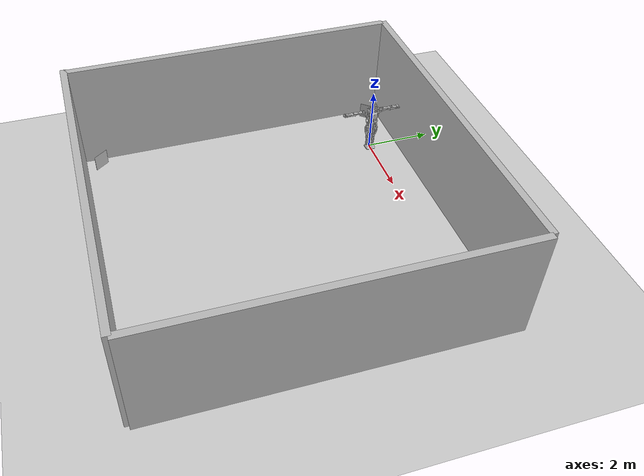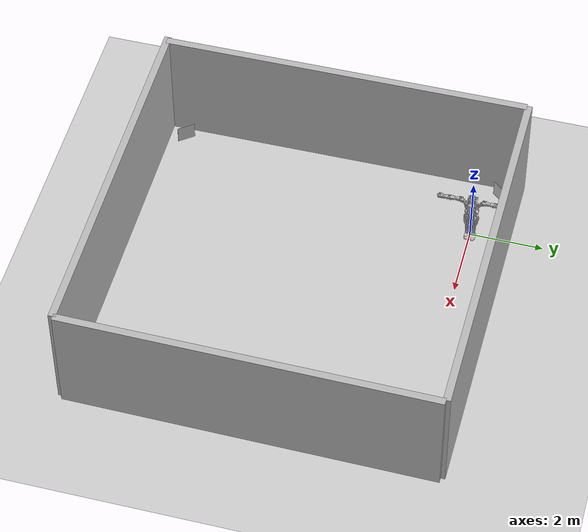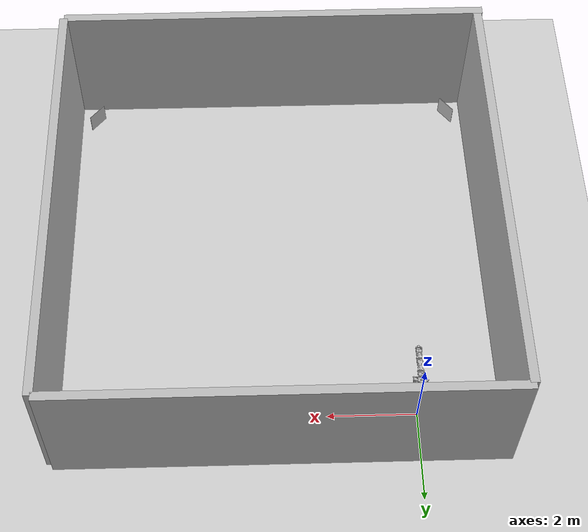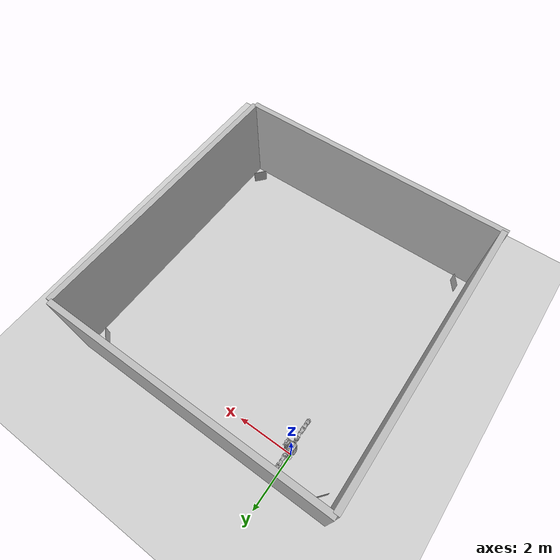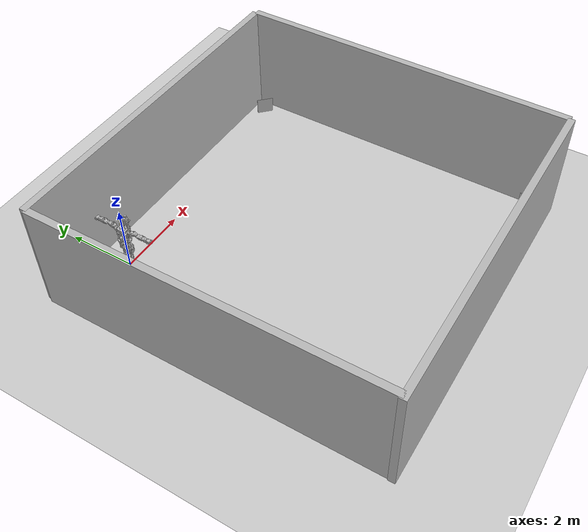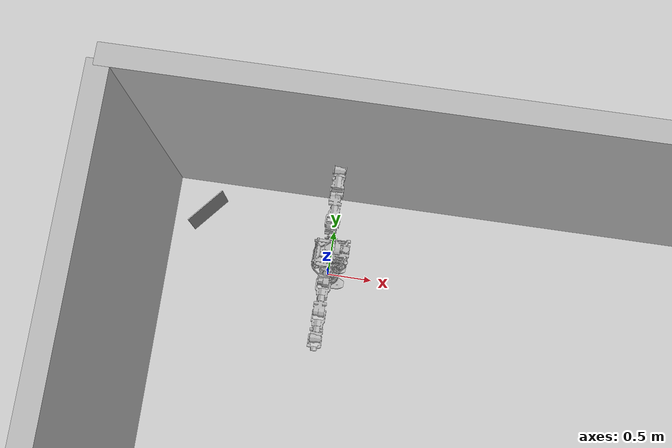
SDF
<sdf version="1.5">
 <world name="default">
  <light name="sun" type="directional">
   <pose>0 0 10 0 -0 0</pose>
   <diffuse>0.8 0.8 0.8 1</diffuse>
   <specular>0.2 0.2 0.2 1</specular>
   <attenuation>
    <range>1000</range>
    <constant>0.9</constant>
    <linear>0.01</linear>
    <quadratic>0.001</quadratic>
   </attenuation>
   <direction>-0.5 0.1 -0.9</direction>
  </light>
  <plugin name="vrc_plugin" filename="libVRCPlugin.so">
   <atlas><model_name>atlas</model_name><pin_link>utorso</pin_link></atlas>
   <drc_vehicle><model_name>golf_cart</model_name><seat_link>chassis</seat_link></drc_vehicle>
   <drc_fire_hose>
    <fire_hose_model>fire_hose</fire_hose_model>
    <coupling_link>coupling</coupling_link>
    <standpipe_model>standpipe</standpipe_model>
    <spout_link>standpipe</spout_link>
    <thread_pitch>-1000</thread_pitch>
    <coupling_relative_pose>1.17038e-05 -0.125623 0.35 -0.0412152 -1.57078 1.61199</coupling_relative_pose>
   </drc_fire_hose>
  </plugin>
  <model name="ground_plane">
   <static>1</static>
   <link name="link">
    <collision name="collision">
     <geometry><plane><normal>0 0 1</normal><size>100 100</size></plane></geometry>
     <surface><friction><ode><mu>100</mu><mu2>50</mu2></ode></friction></surface>
    </collision>
    <visual name="visual">
     <cast_shadows>0</cast_shadows>
     <geometry><plane><normal>0 0 1</normal><size>100 100</size></plane></geometry>
     <material>
      <script><uri>file://media/materials/scripts/gazebo.material</uri><name>Gazebo/Grey</name></script>
     </material>
    </visual>
   </link>
  </model>
  <physics name="default_physics" default="0" type="ode">
   <max_step_size>0.001</max_step_size>
   <real_time_factor>1</real_time_factor>
   <real_time_update_rate>1000</real_time_update_rate>
   <gravity>0 0 -9.8</gravity>
   <magnetic_field>5.5645e-06 2.28758e-05 -4.23884e-05</magnetic_field>
  </physics>
  <scene><ambient>0.4 0.4 0.4 1</ambient><background>0.7 0.7 0.7 1</background><shadows>1</shadows></scene>
  <spherical_coordinates>
   <surface_model>EARTH_WGS84</surface_model>
   <latitude_deg>0</latitude_deg>
   <longitude_deg>0</longitude_deg>
   <elevation>0</elevation>
   <heading_deg>0</heading_deg>
  </spherical_coordinates>
  <model name="cutout_wall">
   <static>1</static>
   <link name="link">
    <pose>0 0 1.4 0 -0 0</pose>
    <collision name="collision">
     <geometry><box><size>10 0.2 3.8</size></box></geometry>
     <surface>
      <contact>
       <collide_without_contact>1</collide_without_contact>
       <collide_without_contact_bitmask>2</collide_without_contact_bitmask>
      </contact>
     </surface>
    </collision>
    <visual name="visual">
     <cast_shadows>0</cast_shadows>
     <geometry><box><size>10 0.2 3.8</size></box></geometry>
     <material>
      <script>
       <uri>model://cutout_wall/materials/scripts</uri>
       <uri>model://cutout_wall/materials/textures</uri>
       <name>drc_practice/cutout_wall</name>
      </script>
     </material>
    </visual>
    <sensor name="mud_contact" type="contact">
     <always_on>1</always_on>
     <update_rate>1000</update_rate>
     <contact><collision>collision</collision><topic>__default_topic__</topic></contact>
    </sensor>
   </link>
   <plugin name="gazebo_mud" filename="libMudPlugin.so">
    <contact_sensor_name>link/mud_contact</contact_sensor_name>
    <stiffness>0.0</stiffness>
    <damping>40.0</damping>
    <contact_surface_bitmask>2</contact_surface_bitmask>
    <link_name>drill::link</link_name>
   </plugin>
   <pose>3 1 0 0 -0 0</pose>
  </model>
  <model name="cutout_wall_0">
   <static>1</static>
   <link name="link">
    <pose>0 0 1.4 0 -0 0</pose>
    <collision name="collision">
     <geometry><box><size>10 0.2 3.8</size></box></geometry>
     <surface>
      <contact>
       <collide_without_contact>1</collide_without_contact>
       <collide_without_contact_bitmask>2</collide_without_contact_bitmask>
      </contact>
     </surface>
    </collision>
    <visual name="visual">
     <cast_shadows>0</cast_shadows>
     <geometry><box><size>10 0.2 3.8</size></box></geometry>
     <material>
      <script>
       <uri>model://cutout_wall/materials/scripts</uri>
       <uri>model://cutout_wall/materials/textures</uri>
       <name>drc_practice/cutout_wall</name>
      </script>
     </material>
    </visual>
    <sensor name="mud_contact" type="contact">
     <always_on>1</always_on>
     <update_rate>1000</update_rate>
     <contact><collision>collision</collision><topic>__default_topic__</topic></contact>
    </sensor>
   </link>
   <plugin name="gazebo_mud" filename="libMudPlugin.so">
    <contact_sensor_name>link/mud_contact</contact_sensor_name>
    <stiffness>0.0</stiffness>
    <damping>40.0</damping>
    <contact_surface_bitmask>2</contact_surface_bitmask>
    <link_name>drill::link</link_name>
   </plugin>
   <pose>-1.94126 -4.0429 0 0 -0 1.57507</pose>
  </model>
  <model name="cutout_wall_1">
   <static>1</static>
   <link name="link">
    <pose>0 0 1.4 0 -0 0</pose>
    <collision name="collision">
     <geometry><box><size>10 0.2 3.8</size></box></geometry>
     <surface>
      <contact>
       <collide_without_contact>1</collide_without_contact>
       <collide_without_contact_bitmask>2</collide_without_contact_bitmask>
      </contact>
     </surface>
    </collision>
    <visual name="visual">
     <cast_shadows>0</cast_shadows>
     <geometry><box><size>10 0.2 3.8</size></box></geometry>
     <material>
      <script>
       <uri>model://cutout_wall/materials/scripts</uri>
       <uri>model://cutout_wall/materials/textures</uri>
       <name>drc_practice/cutout_wall</name>
      </script>
     </material>
    </visual>
    <sensor name="mud_contact" type="contact">
     <always_on>1</always_on>
     <update_rate>1000</update_rate>
     <contact><collision>collision</collision><topic>__default_topic__</topic></contact>
    </sensor>
   </link>
   <plugin name="gazebo_mud" filename="libMudPlugin.so">
    <contact_sensor_name>link/mud_contact</contact_sensor_name>
    <stiffness>0.0</stiffness>
    <damping>40.0</damping>
    <contact_surface_bitmask>2</contact_surface_bitmask>
    <link_name>drill::link</link_name>
   </plugin>
   <pose>2.95415 -9.03799 0 0 -0 0</pose>
  </model>
  <model name="cutout_wall_2">
   <static>1</static>
   <link name="link">
    <pose>0 0 1.4 0 -0 0</pose>
    <collision name="collision">
     <geometry><box><size>10 0.2 3.8</size></box></geometry>
     <surface>
      <contact>
       <collide_without_contact>1</collide_without_contact>
       <collide_without_contact_bitmask>2</collide_without_contact_bitmask>
      </contact>
     </surface>
    </collision>
    <visual name="visual">
     <cast_shadows>0</cast_shadows>
     <geometry><box><size>10 0.2 3.8</size></box></geometry>
     <material>
      <script>
       <uri>model://cutout_wall/materials/scripts</uri>
       <uri>model://cutout_wall/materials/textures</uri>
       <name>drc_practice/cutout_wall</name>
      </script>
     </material>
    </visual>
    <sensor name="mud_contact" type="contact">
     <always_on>1</always_on>
     <update_rate>1000</update_rate>
     <contact><collision>collision</collision><topic>__default_topic__</topic></contact>
    </sensor>
   </link>
   <plugin name="gazebo_mud" filename="libMudPlugin.so">
    <contact_sensor_name>link/mud_contact</contact_sensor_name>
    <stiffness>0.0</stiffness>
    <damping>40.0</damping>
    <contact_surface_bitmask>2</contact_surface_bitmask>
    <link_name>drill::link</link_name>
   </plugin>
   <pose>7.99859 -4.01588 0 0 0 -1.57885</pose>
  </model>
  <model name="atlas">
   <link name="pelvis">
    <inertial>
     <pose>0.0114401 0 0.0268126 0 -0 0</pose>
     <mass>14.3529</mass>
     <inertia>
      <ixx>0.125569</ixx>
      <ixy>0.0008</ixy>
      <ixz>-0.00050004</ixz>
      <iyy>0.0972056</iyy>
      <iyz>-0.0005</iyz>
      <izz>0.117937</izz>
     </inertia>
    </inertial>
    <collision name="pelvis_collision">
     <pose>0.046 0 -0.02 1.5708 -0 0</pose>
     <geometry><cylinder><length>0.06</length><radius>0.11</radius></cylinder></geometry>
     <surface><friction><ode><mu>0.9</mu><mu2>0.9</mu2></ode></friction></surface>
    </collision>
    <collision name="pelvis_collision_pelvis_1">
     <pose>-0.03 0 -0.02 1.5708 -0 0</pose>
     <geometry><cylinder><length>0.06</length><radius>0.11</radius></cylinder></geometry>
     <surface><friction><ode><mu>0.9</mu><mu2>0.9</mu2></ode></friction></surface>
    </collision>
    <collision name="pelvis_collision_pelvis_2">
     <pose>0.01 0.042 0.09 0 -0 0</pose>
     <geometry><cylinder><length>0.05</length><radius>0.16</radius></cylinder></geometry>
     <surface><friction><ode><mu>0.9</mu><mu2>0.9</mu2></ode></friction></surface>
    </collision>
    <collision name="pelvis_collision_pelvis_3">
     <pose>0.01 -0.042 0.09 0 -0 0</pose>
     <geometry><cylinder><length>0.05</length><radius>0.16</radius></cylinder></geometry>
     <surface><friction><ode><mu>0.9</mu><mu2>0.9</mu2></ode></friction></surface>
    </collision>
    <collision name="pelvis_collision_pelvis_4">
     <pose>-0.1 0 -0.05 0 -0 0</pose>
     <geometry><box><size>0.1 0.15 0.2</size></box></geometry>
     <surface><friction><ode><mu>0.9</mu><mu2>0.9</mu2></ode></friction></surface>
    </collision>
    <visual name="pelvis_visual">
     <geometry><mesh><scale>1 1 1</scale><uri>model://atlas_description/meshes/pelvis.dae</uri></mesh></geometry>
    </visual>
    <visual name="pelvis_visual_pelvis_1">
     <pose>0.0599153 0 -0.01415 0 -0 0</pose>
     <geometry><box><size>0.01 0.01 0.01</size></box></geometry>
    </visual>
    <sensor name="imu_sensor" type="imu">
     <always_on>1</always_on>
     <update_rate>1000</update_rate>
     <imu>
      <noise>
       <type>gaussian</type>
       <rate>
        <mean>0</mean>
        <stddev>0.0002</stddev>
        <bias_mean>7.5e-06</bias_mean>
        <bias_stddev>8e-07</bias_stddev>
       </rate>
       <accel><mean>0</mean><stddev>0.017</stddev><bias_mean>0.1</bias_mean><bias_stddev>0.001</bias_stddev></accel>
      </noise>
     </imu>
     <pose>0.0599153 0 -0.01415 0 -0 0</pose>
    </sensor>
   </link>
   <link name="ltorso">
    <pose>-0.0125 0 0 0 -0 0</pose>
    <inertial>
     <pose>-0.0112984 -3.15366e-06 0.0746835 0 -0 0</pose>
     <mass>1.92</mass>
     <inertia>
      <ixx>0.0039092</ixx>
      <ixy>-5.04491e-08</ixy>
      <ixz>-0.000342157</ixz>
      <iyy>0.00341694</iyy>
      <iyz>4.87119e-07</iyz>
      <izz>0.00174492</izz>
     </inertia>
    </inertial>
    <visual name="ltorso_visual">
     <geometry><mesh><scale>1 1 1</scale><uri>model://atlas_description/meshes/ltorso.dae</uri></mesh></geometry>
    </visual>
   </link>
   <joint name="back_lbz" type="revolute">
    <child>ltorso</child>
    <parent>pelvis</parent>
    <axis>
     <xyz>0 0 1</xyz>
     <limit><lower>-0.610865</lower><upper>0.610865</upper><effort>124.016</effort><velocity>12</velocity></limit>
     <dynamics>
      <damping>10</damping>
      <friction>0</friction>
      <spring_reference>0</spring_reference>
      <spring_stiffness>0</spring_stiffness>
     </dynamics>
     <use_parent_model_frame>1</use_parent_model_frame>
    </axis>
    <physics>
     <ode>
      <implicit_spring_damper>1</implicit_spring_damper>
      <cfm_damping>1</cfm_damping>
      <limit><cfm>0</cfm><erp>0.2</erp></limit>
     </ode>
    </physics>
   </joint>
   <link name="mtorso">
    <pose>-0.0125 0 0.09 0 -0 0</pose>
    <inertial>
     <pose>-0.00816266 -0.0131245 0.0305974 0 -0 0</pose>
     <mass>0.55</mass>
     <inertia>
      <ixx>0.000454181</ixx>
      <ixy>-6.10764e-05</ixy>
      <ixz>3.94009e-05</ixz>
      <iyy>0.000483282</iyy>
      <iyz>5.27463e-05</iyz>
      <izz>0.000444215</izz>
     </inertia>
    </inertial>
    <collision name="mtorso_collision">
     <pose>0 0 0 1.5708 -0 0</pose>
     <geometry><cylinder><length>0.03</length><radius>0.017</radius></cylinder></geometry>
     <surface><friction><ode><mu>0.9</mu><mu2>0.9</mu2></ode></friction></surface>
    </collision>
    <collision name="mtorso_collision_mtorso_1">
     <pose>0.0285 0 0.05 -2.65359e-06 1.57079 -2.65359e-06</pose>
     <geometry><cylinder><length>0.02</length><radius>0.015</radius></cylinder></geometry>
     <surface><friction><ode><mu>0.9</mu><mu2>0.9</mu2></ode></friction></surface>
    </collision>
    <collision name="mtorso_collision_mtorso_2">
     <pose>-0.0285 0 0.05 -2.65359e-06 1.57079 -2.65359e-06</pose>
     <geometry><cylinder><length>0.02</length><radius>0.015</radius></cylinder></geometry>
     <surface><friction><ode><mu>0.9</mu><mu2>0.9</mu2></ode></friction></surface>
    </collision>
    <visual name="mtorso_visual">
     <geometry><mesh><scale>1 1 1</scale><uri>model://atlas_description/meshes/mtorso.dae</uri></mesh></geometry>
    </visual>
   </link>
   <joint name="back_mby" type="revolute">
    <child>mtorso</child>
    <parent>ltorso</parent>
    <axis>
     <xyz>0 1 0</xyz>
     <limit><lower>-1.2</lower><upper>1.28</upper><effort>206.843</effort><velocity>12</velocity></limit>
     <dynamics>
      <damping>10</damping>
      <friction>0</friction>
      <spring_reference>0</spring_reference>
      <spring_stiffness>0</spring_stiffness>
     </dynamics>
     <use_parent_model_frame>1</use_parent_model_frame>
    </axis>
    <physics>
     <ode>
      <implicit_spring_damper>1</implicit_spring_damper>
      <cfm_damping>1</cfm_damping>
      <limit><cfm>0</cfm><erp>0.2</erp></limit>
     </ode>
    </physics>
   </joint>
   <link name="utorso">
    <pose>-0.0125 0 0.14 0 -0 0</pose>
    <inertial>
     <pose>0.02 -0.001 0.211 0 -0 0</pose>
     <mass>18.484</mass>
     <inertia>
      <ixx>0.395</ixx>
      <ixy>0</ixy>
      <ixz>0.083</ixz>
      <iyy>1.089</iyy>
      <iyz>-0.003</iyz>
      <izz>0.827</izz>
     </inertia>
    </inertial>
    <collision name="utorso_collision">
     <pose>0.0446 0 0.1869 0 -0 0</pose>
     <geometry><box><size>0.3188 0.24 0.3162</size></box></geometry>
     <surface><friction><ode><mu>0.9</mu><mu2>0.9</mu2></ode></friction></surface>
    </collision>
    <collision name="utorso_collision_utorso_1">
     <pose>0.024 0.16 0.18 -0.5236 0 0</pose>
     <geometry><cylinder><length>0.22375</length><radius>0.0363</radius></cylinder></geometry>
     <surface><friction><ode><mu>0.9</mu><mu2>0.9</mu2></ode></friction></surface>
    </collision>
    <collision name="utorso_collision_utorso_2">
     <pose>0.024 -0.16 0.18 0.5236 -0 0</pose>
     <geometry><cylinder><length>0.22375</length><radius>0.0363</radius></cylinder></geometry>
     <surface><friction><ode><mu>0.9</mu><mu2>0.9</mu2></ode></friction></surface>
    </collision>
    <visual name="utorso_visual">
     <geometry><mesh><scale>1 1 1</scale><uri>model://atlas_description/meshes/utorso.dae</uri></mesh></geometry>
    </visual>
   </link>
   <joint name="back_ubx" type="revolute">
    <child>utorso</child>
    <parent>mtorso</parent>
    <axis>
     <xyz>1 0 0</xyz>
     <limit><lower>-0.790809</lower><upper>0.790809</upper><effort>94.91</effort><velocity>12</velocity></limit>
     <dynamics>
      <damping>10</damping>
      <friction>0</friction>
      <spring_reference>0</spring_reference>
      <spring_stiffness>0</spring_stiffness>
     </dynamics>
     <use_parent_model_frame>1</use_parent_model_frame>
    </axis>
    <physics>
     <ode>
      <implicit_spring_damper>1</implicit_spring_damper>
      <cfm_damping>1</cfm_damping>
      <limit><cfm>0</cfm><erp>0.2</erp></limit>
     </ode>
    </physics>
   </joint>
   <link name="l_clav">
    <pose>0.0115 0.221 0.429 0 -0 0</pose>
    <inertial>
     <pose>0.014 0.058 0.029 0 -0 0</pose>
     <mass>2.369</mass>
     <inertia><ixx>0.004</ixx><ixy>0.001</ixy><ixz>0</ixz><iyy>0.006</iyy><iyz>0</iyz><izz>0.007</izz></inertia>
    </inertial>
    <collision name="l_clav_collision">
     <pose>0 0.0697 0.0261 -2.65359e-06 1.57079 -2.65359e-06</pose>
     <geometry><cylinder><length>0.1525</length><radius>0.045</radius></cylinder></geometry>
     <surface><friction><ode><mu>0.9</mu><mu2>0.9</mu2></ode></friction></surface>
    </collision>
    <collision name="l_clav_collision_l_clav_1">
     <pose>-0.005 -0.0074 -0.0538 1.0472 -0 0</pose>
     <geometry><box><size>0.13 0.15 0.05</size></box></geometry>
     <surface><friction><ode><mu>0.9</mu><mu2>0.9</mu2></ode></friction></surface>
    </collision>
    <visual name="l_clav_visual">
     <pose>0 0 0 1.0472 -0 0</pose>
     <geometry><mesh><scale>1 1 1</scale><uri>model://atlas_description/meshes/l_clav.dae</uri></mesh></geometry>
    </visual>
   </link>
   <joint name="l_arm_usy" type="revolute">
    <child>l_clav</child>
    <parent>utorso</parent>
    <axis>
     <xyz>0 0.5 0.866025</xyz>
     <limit><lower>-1.9635</lower><upper>1.9635</upper><effort>212</effort><velocity>12</velocity></limit>
     <dynamics>
      <damping>1</damping>
      <friction>0</friction>
      <spring_reference>0</spring_reference>
      <spring_stiffness>0</spring_stiffness>
     </dynamics>
     <use_parent_model_frame>1</use_parent_model_frame>
    </axis>
    <physics>
     <ode>
      <implicit_spring_damper>1</implicit_spring_damper>
      <cfm_damping>1</cfm_damping>
      <limit><cfm>0</cfm><erp>0.2</erp></limit>
     </ode>
    </physics>
   </joint>
   <link name="l_scap">
    <pose>0.0115 0.296 0.465 0 -0 0</pose>
    <inertial>
     <pose>-0.002 0.108 0 0 -0 0</pose>
     <mass>2.707</mass>
     <inertia><ixx>0.01</ixx><ixy>0</ixy><ixz>0</ixz><iyy>0.005</iyy><iyz>0</iyz><izz>0.013</izz></inertia>
    </inertial>
    <collision name="l_scap_collision">
     <pose>0.001 0.12651 0.01521 1.5708 -0 0</pose>
     <geometry><cylinder><length>0.125</length><radius>0.045</radius></cylinder></geometry>
     <surface><friction><ode><mu>0.9</mu><mu2>0.9</mu2></ode></friction></surface>
    </collision>
    <collision name="l_scap_collision_l_scap_1">
     <pose>0.001 0.05 0.016 0 -0 0</pose>
     <geometry><box><size>0.15 0.15 0.06</size></box></geometry>
     <surface><friction><ode><mu>0.9</mu><mu2>0.9</mu2></ode></friction></surface>
    </collision>
    <visual name="l_scap_visual">
     <geometry><mesh><scale>1 1 1</scale><uri>model://atlas_description/meshes/l_scap.dae</uri></mesh></geometry>
    </visual>
   </link>
   <joint name="l_arm_shx" type="revolute">
    <child>l_scap</child>
    <parent>l_clav</parent>
    <axis>
     <xyz>1 0 0</xyz>
     <limit><lower>-1.39626</lower><upper>1.74533</upper><effort>170</effort><velocity>12</velocity></limit>
     <dynamics>
      <damping>1</damping>
      <friction>0</friction>
      <spring_reference>0</spring_reference>
      <spring_stiffness>0</spring_stiffness>
     </dynamics>
     <use_parent_model_frame>1</use_parent_model_frame>
    </axis>
    <physics>
     <ode>
      <implicit_spring_damper>1</implicit_spring_damper>
      <cfm_damping>1</cfm_damping>
      <limit><cfm>0</cfm><erp>0.2</erp></limit>
     </ode>
    </physics>
   </joint>
   <link name="l_uarm">
    <pose>0.0115 0.481 0.465 0 -0 0</pose>
    <inertial>
     <pose>0.007 0.114 0.008 0 -0 0</pose>
     <mass>1.881</mass>
     <inertia><ixx>0.002</ixx><ixy>0</ixy><ixz>0</ixz><iyy>0.003</iyy><iyz>0</iyz><izz>0.003</izz></inertia>
    </inertial>
    <collision name="l_uarm_collision">
     <pose>0.001 0.111 0 3.14159 1.57079 3.14159</pose>
     <geometry><cylinder><length>0.125</length><radius>0.045</radius></cylinder></geometry>
     <surface><friction><ode><mu>0.9</mu><mu2>0.9</mu2></ode></friction></surface>
    </collision>
    <collision name="l_uarm_collision_l_uarm_1">
     <pose>0.001 0.043 0.01 -2.65359e-06 1.57079 -2.65359e-06</pose>
     <geometry><box><size>0.04 0.07 0.13</size></box></geometry>
     <surface><friction><ode><mu>0.9</mu><mu2>0.9</mu2></ode></friction></surface>
    </collision>
    <visual name="l_uarm_visual">
     <geometry><mesh><scale>1 1 1</scale><uri>model://atlas_description/meshes/l_uarm.dae</uri></mesh></geometry>
    </visual>
   </link>
   <joint name="l_arm_ely" type="revolute">
    <child>l_uarm</child>
    <parent>l_scap</parent>
    <axis>
     <xyz>0 1 0</xyz>
     <limit><lower>0</lower><upper>3.14159</upper><effort>114</effort><velocity>12</velocity></limit>
     <dynamics>
      <damping>1</damping>
      <friction>0</friction>
      <spring_reference>0</spring_reference>
      <spring_stiffness>0</spring_stiffness>
     </dynamics>
     <use_parent_model_frame>1</use_parent_model_frame>
    </axis>
    <physics>
     <ode>
      <implicit_spring_damper>1</implicit_spring_damper>
      <cfm_damping>1</cfm_damping>
      <limit><cfm>0</cfm><erp>0.2</erp></limit>
     </ode>
    </physics>
   </joint>
   <link name="l_larm">
    <pose>0.0115 0.602 0.478 0 -0 0</pose>
    <inertial>
     <pose>-0.003 0.099 -0.014 0 -0 0</pose>
     <mass>2.148</mass>
     <inertia><ixx>0.005</ixx><ixy>0</ixy><ixz>0</ixz><iyy>0.003</iyy><iyz>0</iyz><izz>0.006</izz></inertia>
    </inertial>
    <collision name="l_larm_collision">
     <pose>0.001 0.127 0 1.5708 -0 0</pose>
     <geometry><cylinder><length>0.125</length><radius>0.045</radius></cylinder></geometry>
     <surface><friction><ode><mu>0.9</mu><mu2>0.9</mu2></ode></friction></surface>
    </collision>
    <collision name="l_larm_collision_l_larm_1">
     <pose>0.001 0.051 0 0 -0 0</pose>
     <geometry><box><size>0.135 0.15 0.06</size></box></geometry>
     <surface><friction><ode><mu>0.9</mu><mu2>0.9</mu2></ode></friction></surface>
    </collision>
    <visual name="l_larm_visual">
     <geometry><mesh><scale>1 1 1</scale><uri>model://atlas_description/meshes/l_larm.dae</uri></mesh></geometry>
    </visual>
   </link>
   <joint name="l_arm_elx" type="revolute">
    <child>l_larm</child>
    <parent>l_uarm</parent>
    <axis>
     <xyz>1 0 0</xyz>
     <limit><lower>0</lower><upper>2.35619</upper><effort>114</effort><velocity>12</velocity></limit>
     <dynamics>
      <damping>1</damping>
      <friction>0</friction>
      <spring_reference>0</spring_reference>
      <spring_stiffness>0</spring_stiffness>
     </dynamics>
     <use_parent_model_frame>1</use_parent_model_frame>
    </axis>
    <physics>
     <ode>
      <implicit_spring_damper>1</implicit_spring_damper>
      <cfm_damping>1</cfm_damping>
      <limit><cfm>0</cfm><erp>0.2</erp></limit>
     </ode>
    </physics>
   </joint>
   <link name="l_farm">
    <pose>0.0115 0.79 0.465 0 -0 0</pose>
    <inertial>
     <pose>0 0.041 0 0 -0 0</pose>
     <mass>0.981</mass>
     <inertia><ixx>0.003</ixx><ixy>0</ixy><ixz>0</ixz><iyy>0.001</iyy><iyz>0</iyz><izz>0.003</izz></inertia>
    </inertial>
    <collision name="l_farm_collision">
     <pose>0 0.065 0.004 3.14159 1.57079 3.14159</pose>
     <geometry><cylinder><length>0.125</length><radius>0.045</radius></cylinder></geometry>
     <surface><friction><ode><mu>0.9</mu><mu2>0.9</mu2></ode></friction></surface>
    </collision>
    <collision name="l_farm_collision_l_farm_1">
     <pose>0.001 0.015 -0.002 0 -0 0</pose>
     <geometry><box><size>0.135 0.1 0.045</size></box></geometry>
     <surface><friction><ode><mu>0.9</mu><mu2>0.9</mu2></ode></friction></surface>
    </collision>
    <visual name="l_farm_visual">
     <pose>0 -0.06 0 0 -0 0</pose>
     <geometry><mesh><scale>1 1 1</scale><uri>model://atlas_description/meshes/l_farm.dae</uri></mesh></geometry>
    </visual>
   </link>
   <joint name="l_arm_uwy" type="revolute">
    <child>l_farm</child>
    <parent>l_larm</parent>
    <axis>
     <xyz>0 1 0</xyz>
     <limit><lower>-1.571</lower><upper>1.571</upper><effort>114</effort><velocity>12</velocity></limit>
     <dynamics>
      <damping>1</damping>
      <friction>0</friction>
      <spring_reference>0</spring_reference>
      <spring_stiffness>0</spring_stiffness>
     </dynamics>
     <use_parent_model_frame>1</use_parent_model_frame>
    </axis>
    <physics>
     <ode>
      <implicit_spring_damper>1</implicit_spring_damper>
      <cfm_damping>1</cfm_damping>
      <limit><cfm>0</cfm><erp>0.2</erp></limit>
     </ode>
    </physics>
   </joint>
   <link name="l_hand">
    <pose>0.0115 0.848 0.465 0 -0 0</pose>
    <inertial>
     <pose>0 0.093 0 0 -0 0</pose>
     <mass>2.263</mass>
     <inertia><ixx>0.01</ixx><ixy>0</ixy><ixz>0</ixz><iyy>0.002</iyy><iyz>0</iyz><izz>0.01</izz></inertia>
    </inertial>
    <collision name="l_hand_collision">
     <pose>0.001 0.1 0.01 1.5708 -0 0</pose>
     <geometry><cylinder><length>0.05</length><radius>0.03</radius></cylinder></geometry>
     <surface><friction><ode><mu>0.9</mu><mu2>0.9</mu2></ode></friction></surface>
    </collision>
    <collision name="l_hand_collision_l_hand_1">
     <pose>0.001 0.05 0.01 0 -0 0</pose>
     <geometry><box><size>0.13 0.09 0.07</size></box></geometry>
     <surface><friction><ode><mu>0.9</mu><mu2>0.9</mu2></ode></friction></surface>
    </collision>
    <visual name="l_hand_visual">
     <geometry><mesh><scale>1 1 1</scale><uri>model://atlas_description/meshes/l_hand.dae</uri></mesh></geometry>
    </visual>
   </link>
   <joint name="l_arm_mwx" type="revolute">
    <child>l_hand</child>
    <parent>l_farm</parent>
    <axis>
     <xyz>1 0 0</xyz>
     <limit><lower>-0.436</lower><upper>1.571</upper><effort>60</effort><velocity>12</velocity></limit>
     <dynamics>
      <damping>1</damping>
      <friction>0</friction>
      <spring_reference>0</spring_reference>
      <spring_stiffness>0</spring_stiffness>
     </dynamics>
     <use_parent_model_frame>1</use_parent_model_frame>
    </axis>
    <physics>
     <provide_feedback>1</provide_feedback>
     <ode>
      <provide_feedback>1</provide_feedback>
      <limit><cfm>0</cfm><erp>0.2</erp></limit>
      <implicit_spring_damper>1</implicit_spring_damper>
      <cfm_damping>1</cfm_damping>
     </ode>
    </physics>
   </joint>
   <link name="head">
    <pose>0.20422 0 0.67796 0 -0 0</pose>
    <inertial>
     <pose>-0.0754942 3.38765e-05 0.0277411 0 -0 0</pose>
     <mass>1.41991</mass>
     <inertia>
      <ixx>0.00397627</ixx>
      <ixy>-1.51324e-06</ixy>
      <ixz>-0.000892818</ixz>
      <iyy>0.00412515</iyy>
      <iyz>-6.83342e-07</iyz>
      <izz>0.00353178</izz>
     </inertia>
    </inertial>
    <collision name="head_collision">
     <pose>-0.0503 0 -0.00195 0 -0 0</pose>
     <geometry><box><size>0.1311 0.12 0.0591</size></box></geometry>
     <surface><friction><ode><mu>0.9</mu><mu2>0.9</mu2></ode></friction></surface>
    </collision>
    <collision name="head_collision_head_1">
     <pose>-0.093 0 0.0868 0 -0 0</pose>
     <geometry><box><size>0.0468 0.12 0.1184</size></box></geometry>
     <surface><friction><ode><mu>0.9</mu><mu2>0.9</mu2></ode></friction></surface>
    </collision>
    <visual name="head_visual">
     <geometry>
      <mesh><scale>1 1 1</scale><uri>model://multisense_sl_description/meshes/head.dae</uri></mesh>
     </geometry>
    </visual>
    <visual name="head_visual_head_1">
     <pose>-0.0475 0.035 0 0 -0 0</pose>
     <geometry><box><size>0.01 0.01 0.01</size></box></geometry>
    </visual>
    <sensor name="head_imu_sensor" type="imu">
     <always_on>1</always_on>
     <update_rate>1000</update_rate>
     <imu>
      <noise>
       <type>gaussian</type>
       <rate>
        <mean>0</mean>
        <stddev>0.0002</stddev>
        <bias_mean>7.5e-06</bias_mean>
        <bias_stddev>8e-07</bias_stddev>
       </rate>
       <accel><mean>0</mean><stddev>0.017</stddev><bias_mean>0.1</bias_mean><bias_stddev>0.001</bias_stddev></accel>
      </noise>
     </imu>
     <pose>-0.0475 0.035 0 0 -0 0</pose>
    </sensor>
    <sensor name="stereo_camera" type="multicamera">
     <update_rate>30</update_rate>
     <camera name="left">
      <horizontal_fov>1.39626</horizontal_fov>
      <image><width>800</width><height>800</height><format>R8G8B8</format></image>
      <clip><near>0.02</near><far>300</far></clip>
      <noise><type>gaussian</type><mean>0</mean><stddev>0.007</stddev></noise>
     </camera>
     <camera name="right">
      <pose>0 -0.07 0 0 -0 0</pose>
      <horizontal_fov>1.39626</horizontal_fov>
      <image><width>800</width><height>800</height><format>R8G8B8</format></image>
      <clip><near>0.02</near><far>300</far></clip>
      <noise><type>gaussian</type><mean>0</mean><stddev>0.007</stddev></noise>
     </camera>
     <plugin name="stereo_camera_controller" filename="libgazebo_ros_multicamera.so">
      <alwaysOn>true</alwaysOn>
      <updateRate>0.0</updateRate>
      <cameraName>multisense_sl</cameraName>
      <imageTopicName>image_raw</imageTopicName>
      <cameraInfoTopicName>camera_info</cameraInfoTopicName>
      <frameName>left_camera_optical_frame</frameName>
      <hackBaseline>0.07</hackBaseline>
      <distortionK1>0.0</distortionK1>
      <distortionK2>0.0</distortionK2>
      <distortionK3>0.0</distortionK3>
      <distortionT1>0.0</distortionT1>
      <distortionT2>0.0</distortionT2>
     </plugin>
     <pose>0 0.035 -0.002 0 -0 0</pose>
    </sensor>
   </link>
   <joint name="neck_ay" type="revolute">
    <child>head</child>
    <parent>utorso</parent>
    <axis>
     <xyz>0 1 0</xyz>
     <limit><lower>-0.610865</lower><upper>1.13446</upper><effort>5</effort><velocity>12</velocity></limit>
     <dynamics>
      <damping>1</damping>
      <friction>0</friction>
      <spring_reference>0</spring_reference>
      <spring_stiffness>0</spring_stiffness>
     </dynamics>
     <use_parent_model_frame>1</use_parent_model_frame>
    </axis>
    <physics>
     <ode>
      <implicit_spring_damper>1</implicit_spring_damper>
      <cfm_damping>1</cfm_damping>
      <limit><cfm>0</cfm><erp>0.2</erp></limit>
     </ode>
    </physics>
   </joint>
   <link name="hokuyo_link">
    <pose>0.15962 0 0.76596 0 -0 0</pose>
    <inertial>
     <pose>0.0324349 0.0004084 -0.0041783 0 -0 0</pose>
     <mass>0.057664</mass>
     <inertia>
      <ixx>3.8183e-05</ixx>
      <ixy>4.9927e-08</ixy>
      <ixz>1.1003e-05</ixz>
      <iyy>4.3437e-05</iyy>
      <iyz>-9.8165e-09</iyz>
      <izz>4.2686e-05</izz>
     </inertia>
    </inertial>
    <collision name="hokuyo_link_collision">
     <pose>0.01885 0 -0.02119 0 -0 0</pose>
     <geometry><box><size>0.08 0.06 0.04238</size></box></geometry>
     <surface><friction><ode><mu>0.9</mu><mu2>0.9</mu2></ode></friction></surface>
    </collision>
    <collision name="hokuyo_link_collision_hokuyo_link_1">
     <pose>0.03 0 0.0235 0 -0 0</pose>
     <geometry><cylinder><length>0.047</length><radius>0.024425</radius></cylinder></geometry>
     <surface><friction><ode><mu>0.9</mu><mu2>0.9</mu2></ode></friction></surface>
    </collision>
    <visual name="hokuyo_link_visual">
     <pose>0.045 -0.0261018 -0.0834237 -0.314 0 0</pose>
     <geometry>
      <mesh><scale>1 1 1</scale><uri>model://multisense_sl_description/meshes/head_camera.dae</uri></mesh>
     </geometry>
    </visual>
    <sensor name="head_hokuyo_sensor" type="gpu_ray">
     <visualize>0</visualize>
     <update_rate>40</update_rate>
     <ray>
      <scan>
       <horizontal>
        <samples>720</samples>
        <resolution>1</resolution>
        <min_angle>-1.5708</min_angle>
        <max_angle>1.5708</max_angle>
       </horizontal>
      </scan>
      <range><min>0.1</min><max>30</max><resolution>0.01</resolution></range>
      <noise><type>gaussian</type><mean>0</mean><stddev>0.01</stddev></noise>
     </ray>
     <plugin name="gazebo_ros_head_hokuyo_controller" filename="libgazebo_ros_gpu_laser.so">
      <topicName>/laser/scan</topicName>
      <frameName>head_hokuyo_frame</frameName>
     </plugin>
     <pose>0.03 0 0.015 0 -0 0</pose>
    </sensor>
   </link>
   <joint name="hokuyo_joint" type="revolute">
    <child>hokuyo_link</child>
    <parent>head</parent>
    <axis>
     <xyz>1 0 0</xyz>
     <limit><lower>-1e+16</lower><upper>1e+16</upper></limit>
     <dynamics>
      <damping>0.01</damping>
      <friction>0</friction>
      <spring_reference>0</spring_reference>
      <spring_stiffness>0</spring_stiffness>
     </dynamics>
     <use_parent_model_frame>1</use_parent_model_frame>
    </axis>
    <physics>
     <ode>
      <implicit_spring_damper>1</implicit_spring_damper>
      <cfm_damping>1</cfm_damping>
      <limit><cfm>0</cfm><erp>0.2</erp></limit>
     </ode>
    </physics>
   </joint>
   <link name="r_clav">
    <pose>0.0115 -0.221 0.429 0 -0 0</pose>
    <inertial>
     <pose>0.014 -0.058 0.029 0 -0 0</pose>
     <mass>2.369</mass>
     <inertia><ixx>0.004</ixx><ixy>-0.001</ixy><ixz>0</ixz><iyy>0.006</iyy><iyz>0</iyz><izz>0.007</izz></inertia>
    </inertial>
    <collision name="r_clav_collision">
     <pose>0 -0.0697 0.0261 -2.65359e-06 1.57079 -2.65359e-06</pose>
     <geometry><cylinder><length>0.1525</length><radius>0.045</radius></cylinder></geometry>
     <surface><friction><ode><mu>0.9</mu><mu2>0.9</mu2></ode></friction></surface>
    </collision>
    <collision name="r_clav_collision_r_clav_1">
     <pose>-0.005 0.0074 -0.0538 -1.0472 0 0</pose>
     <geometry><box><size>0.13 0.15 0.05</size></box></geometry>
     <surface><friction><ode><mu>0.9</mu><mu2>0.9</mu2></ode></friction></surface>
    </collision>
    <visual name="r_clav_visual">
     <pose>0 0 0 -1.0472 0 0</pose>
     <geometry><mesh><scale>1 1 1</scale><uri>model://atlas_description/meshes/r_clav.dae</uri></mesh></geometry>
    </visual>
   </link>
   <joint name="r_arm_usy" type="revolute">
    <child>r_clav</child>
    <parent>utorso</parent>
    <axis>
     <xyz>0 0.5 -0.866025</xyz>
     <limit><lower>-1.9635</lower><upper>1.9635</upper><effort>212</effort><velocity>12</velocity></limit>
     <dynamics>
      <damping>1</damping>
      <friction>0</friction>
      <spring_reference>0</spring_reference>
      <spring_stiffness>0</spring_stiffness>
     </dynamics>
     <use_parent_model_frame>1</use_parent_model_frame>
    </axis>
    <physics>
     <ode>
      <implicit_spring_damper>1</implicit_spring_damper>
      <cfm_damping>1</cfm_damping>
      <limit><cfm>0</cfm><erp>0.2</erp></limit>
     </ode>
    </physics>
   </joint>
   <link name="r_scap">
    <pose>0.0115 -0.296 0.465 0 -0 0</pose>
    <inertial>
     <pose>-0.002 -0.108 0 0 -0 0</pose>
     <mass>2.707</mass>
     <inertia><ixx>0.01</ixx><ixy>0</ixy><ixz>0</ixz><iyy>0.005</iyy><iyz>0</iyz><izz>0.013</izz></inertia>
    </inertial>
    <collision name="r_scap_collision">
     <pose>0.001 -0.12651 0.01521 1.5708 -0 0</pose>
     <geometry><cylinder><length>0.125</length><radius>0.045</radius></cylinder></geometry>
     <surface><friction><ode><mu>0.9</mu><mu2>0.9</mu2></ode></friction></surface>
    </collision>
    <collision name="r_scap_collision_r_scap_1">
     <pose>0.001 -0.05 0.016 0 -0 0</pose>
     <geometry><box><size>0.15 0.15 0.06</size></box></geometry>
     <surface><friction><ode><mu>0.9</mu><mu2>0.9</mu2></ode></friction></surface>
    </collision>
    <visual name="r_scap_visual">
     <geometry><mesh><scale>1 1 1</scale><uri>model://atlas_description/meshes/r_scap.dae</uri></mesh></geometry>
    </visual>
   </link>
   <joint name="r_arm_shx" type="revolute">
    <child>r_scap</child>
    <parent>r_clav</parent>
    <axis>
     <xyz>1 0 0</xyz>
     <limit><lower>-1.74533</lower><upper>1.39626</upper><effort>170</effort><velocity>12</velocity></limit>
     <dynamics>
      <damping>1</damping>
      <friction>0</friction>
      <spring_reference>0</spring_reference>
      <spring_stiffness>0</spring_stiffness>
     </dynamics>
     <use_parent_model_frame>1</use_parent_model_frame>
    </axis>
    <physics>
     <ode>
      <implicit_spring_damper>1</implicit_spring_damper>
      <cfm_damping>1</cfm_damping>
      <limit><cfm>0</cfm><erp>0.2</erp></limit>
     </ode>
    </physics>
   </joint>
   <link name="r_uarm">
    <pose>0.0115 -0.481 0.465 0 -0 0</pose>
    <inertial>
     <pose>0.007 -0.114 0.008 0 -0 0</pose>
     <mass>1.881</mass>
     <inertia><ixx>0.002</ixx><ixy>0</ixy><ixz>0</ixz><iyy>0.003</iyy><iyz>0</iyz><izz>0.003</izz></inertia>
    </inertial>
    <collision name="r_uarm_collision">
     <pose>0.001 -0.111 0 3.14159 1.57079 3.14159</pose>
     <geometry><cylinder><length>0.125</length><radius>0.045</radius></cylinder></geometry>
     <surface><friction><ode><mu>0.9</mu><mu2>0.9</mu2></ode></friction></surface>
    </collision>
    <collision name="r_uarm_collision_r_uarm_1">
     <pose>0.001 -0.043 0.01 -2.65359e-06 1.57079 -2.65359e-06</pose>
     <geometry><box><size>0.04 0.07 0.13</size></box></geometry>
     <surface><friction><ode><mu>0.9</mu><mu2>0.9</mu2></ode></friction></surface>
    </collision>
    <visual name="r_uarm_visual">
     <geometry><mesh><scale>1 1 1</scale><uri>model://atlas_description/meshes/r_uarm.dae</uri></mesh></geometry>
    </visual>
   </link>
   <joint name="r_arm_ely" type="revolute">
    <child>r_uarm</child>
    <parent>r_scap</parent>
    <axis>
     <xyz>0 1 0</xyz>
     <limit><lower>0</lower><upper>3.14159</upper><effort>114</effort><velocity>12</velocity></limit>
     <dynamics>
      <damping>1</damping>
      <friction>0</friction>
      <spring_reference>0</spring_reference>
      <spring_stiffness>0</spring_stiffness>
     </dynamics>
     <use_parent_model_frame>1</use_parent_model_frame>
    </axis>
    <physics>
     <ode>
      <implicit_spring_damper>1</implicit_spring_damper>
      <cfm_damping>1</cfm_damping>
      <limit><cfm>0</cfm><erp>0.2</erp></limit>
     </ode>
    </physics>
   </joint>
   <link name="r_larm">
    <pose>0.0115 -0.602 0.478 0 -0 0</pose>
    <inertial>
     <pose>-0.003 -0.099 -0.014 0 -0 0</pose>
     <mass>2.148</mass>
     <inertia><ixx>0.005</ixx><ixy>0</ixy><ixz>0</ixz><iyy>0.003</iyy><iyz>0</iyz><izz>0.006</izz></inertia>
    </inertial>
    <collision name="r_larm_collision">
     <pose>0.001 -0.127 0 1.5708 -0 0</pose>
     <geometry><cylinder><length>0.125</length><radius>0.045</radius></cylinder></geometry>
     <surface><friction><ode><mu>0.9</mu><mu2>0.9</mu2></ode></friction></surface>
    </collision>
    <collision name="r_larm_collision_r_larm_1">
     <pose>0.001 -0.051 0 0 -0 0</pose>
     <geometry><box><size>0.135 0.15 0.06</size></box></geometry>
     <surface><friction><ode><mu>0.9</mu><mu2>0.9</mu2></ode></friction></surface>
    </collision>
    <visual name="r_larm_visual">
     <geometry><mesh><scale>1 1 1</scale><uri>model://atlas_description/meshes/r_larm.dae</uri></mesh></geometry>
    </visual>
   </link>
   <joint name="r_arm_elx" type="revolute">
    <child>r_larm</child>
    <parent>r_uarm</parent>
    <axis>
     <xyz>1 0 0</xyz>
     <limit><lower>-2.35619</lower><upper>0</upper><effort>114</effort><velocity>12</velocity></limit>
     <dynamics>
      <damping>1</damping>
      <friction>0</friction>
      <spring_reference>0</spring_reference>
      <spring_stiffness>0</spring_stiffness>
     </dynamics>
     <use_parent_model_frame>1</use_parent_model_frame>
    </axis>
    <physics>
     <ode>
      <implicit_spring_damper>1</implicit_spring_damper>
      <cfm_damping>1</cfm_damping>
      <limit><cfm>0</cfm><erp>0.2</erp></limit>
     </ode>
    </physics>
   </joint>
   <link name="r_farm">
    <pose>0.0115 -0.79 0.465 0 -0 0</pose>
    <inertial>
     <pose>0 -0.041 0 0 -0 0</pose>
     <mass>0.981</mass>
     <inertia><ixx>0.003</ixx><ixy>0</ixy><ixz>0</ixz><iyy>0.001</iyy><iyz>0</iyz><izz>0.003</izz></inertia>
    </inertial>
    <collision name="r_farm_collision">
     <pose>0 -0.065 0.004 3.14159 1.57079 3.14159</pose>
     <geometry><cylinder><length>0.125</length><radius>0.045</radius></cylinder></geometry>
     <surface><friction><ode><mu>0.9</mu><mu2>0.9</mu2></ode></friction></surface>
    </collision>
    <collision name="r_farm_collision_r_farm_1">
     <pose>0.001 -0.015 -0.002 0 -0 0</pose>
     <geometry><box><size>0.135 0.1 0.045</size></box></geometry>
     <surface><friction><ode><mu>0.9</mu><mu2>0.9</mu2></ode></friction></surface>
    </collision>
    <visual name="r_farm_visual">
     <pose>0 0.06 0 0 -0 0</pose>
     <geometry><mesh><scale>1 1 1</scale><uri>model://atlas_description/meshes/r_farm.dae</uri></mesh></geometry>
    </visual>
   </link>
   <joint name="r_arm_uwy" type="revolute">
    <child>r_farm</child>
    <parent>r_larm</parent>
    <axis>
     <xyz>0 1 0</xyz>
     <limit><lower>-1.571</lower><upper>1.571</upper><effort>114</effort><velocity>12</velocity></limit>
     <dynamics>
      <damping>1</damping>
      <friction>0</friction>
      <spring_reference>0</spring_reference>
      <spring_stiffness>0</spring_stiffness>
     </dynamics>
     <use_parent_model_frame>1</use_parent_model_frame>
    </axis>
    <physics>
     <ode>
      <implicit_spring_damper>1</implicit_spring_damper>
      <cfm_damping>1</cfm_damping>
      <limit><cfm>0</cfm><erp>0.2</erp></limit>
     </ode>
    </physics>
   </joint>
   <link name="r_hand">
    <pose>0.0115 -0.848 0.465 0 -0 0</pose>
    <inertial>
     <pose>0 -0.093 0 0 -0 0</pose>
     <mass>2.263</mass>
     <inertia><ixx>0.01</ixx><ixy>0</ixy><ixz>0</ixz><iyy>0.002</iyy><iyz>0</iyz><izz>0.01</izz></inertia>
    </inertial>
    <collision name="r_hand_collision">
     <pose>0.001 -0.1 0.01 1.5708 -0 0</pose>
     <geometry><cylinder><length>0.05</length><radius>0.03</radius></cylinder></geometry>
     <surface><friction><ode><mu>0.9</mu><mu2>0.9</mu2></ode></friction></surface>
    </collision>
    <collision name="r_hand_collision_r_hand_1">
     <pose>0.001 -0.05 0.01 0 -0 0</pose>
     <geometry><box><size>0.13 0.09 0.07</size></box></geometry>
     <surface><friction><ode><mu>0.9</mu><mu2>0.9</mu2></ode></friction></surface>
    </collision>
    <visual name="r_hand_visual">
     <geometry><mesh><scale>1 1 1</scale><uri>model://atlas_description/meshes/r_hand.dae</uri></mesh></geometry>
    </visual>
   </link>
   <joint name="r_arm_mwx" type="revolute">
    <child>r_hand</child>
    <parent>r_farm</parent>
    <axis>
     <xyz>1 0 0</xyz>
     <limit><lower>-1.571</lower><upper>0.436</upper><effort>60</effort><velocity>12</velocity></limit>
     <dynamics>
      <damping>1</damping>
      <friction>0</friction>
      <spring_reference>0</spring_reference>
      <spring_stiffness>0</spring_stiffness>
     </dynamics>
     <use_parent_model_frame>1</use_parent_model_frame>
    </axis>
    <physics>
     <provide_feedback>1</provide_feedback>
     <ode>
      <provide_feedback>1</provide_feedback>
      <limit><cfm>0</cfm><erp>0.2</erp></limit>
      <implicit_spring_damper>1</implicit_spring_damper>
      <cfm_damping>1</cfm_damping>
     </ode>
    </physics>
   </joint>
   <link name="l_uglut">
    <pose>0 0.089 0 0 -0 0</pose>
    <inertial>
     <pose>0.00529262 -0.00344732 0.00313046 0 -0 0</pose>
     <mass>0.5166</mass>
     <inertia>
      <ixx>0.00074276</ixx>
      <ixy>-3.79607e-08</ixy>
      <ixz>-2.79549e-05</ixz>
      <iyy>0.000688179</iyy>
      <iyz>-3.2735e-08</iyz>
      <izz>0.00041242</izz>
     </inertia>
    </inertial>
    <collision name="l_uglut_collision">
     <pose>0 0 0 -2.65359e-06 1.57079 -2.65359e-06</pose>
     <geometry><cylinder><length>0.078396</length><radius>0.019096</radius></cylinder></geometry>
     <surface><friction><ode><mu>0.9</mu><mu2>0.9</mu2></ode></friction></surface>
    </collision>
    <collision name="l_uglut_collision_l_uglut_1">
     <geometry><cylinder><length>0.080842</length><radius>0.019841</radius></cylinder></geometry>
     <surface><friction><ode><mu>0.9</mu><mu2>0.9</mu2></ode></friction></surface>
    </collision>
    <visual name="l_uglut_visual">
     <geometry><mesh><scale>1 1 1</scale><uri>model://atlas_description/meshes/l_uglut.dae</uri></mesh></geometry>
    </visual>
   </link>
   <joint name="l_leg_uhz" type="revolute">
    <child>l_uglut</child>
    <parent>pelvis</parent>
    <axis>
     <xyz>0 0 1</xyz>
     <limit><lower>-0.32</lower><upper>1.14</upper><effort>110</effort><velocity>12</velocity></limit>
     <dynamics>
      <damping>1</damping>
      <friction>0</friction>
      <spring_reference>0</spring_reference>
      <spring_stiffness>0</spring_stiffness>
     </dynamics>
     <use_parent_model_frame>1</use_parent_model_frame>
    </axis>
    <physics>
     <ode>
      <implicit_spring_damper>1</implicit_spring_damper>
      <cfm_damping>1</cfm_damping>
      <limit><cfm>0</cfm><erp>0.2</erp></limit>
     </ode>
    </physics>
   </joint>
   <link name="l_lglut">
    <pose>0 0.089 0 0 -0 0</pose>
    <inertial>
     <pose>0.0133341 0.0170484 -0.0312052 0 -0 0</pose>
     <mass>0.69</mass>
     <inertia>
      <ixx>0.000691326</ixx>
      <ixy>-2.24344e-05</ixy>
      <ixz>2.50508e-06</ixz>
      <iyy>0.00126856</iyy>
      <iyz>0.000137862</iyz>
      <izz>0.00106487</izz>
     </inertia>
    </inertial>
    <collision name="l_lglut_collision">
     <pose>0.049968 0.022488 -0.0501165 1.5708 -0 0</pose>
     <geometry><cylinder><length>0.060306</length><radius>0.0200969</radius></cylinder></geometry>
     <surface><friction><ode><mu>0.9</mu><mu2>0.9</mu2></ode></friction></surface>
    </collision>
    <collision name="l_lglut_collision_l_lglut_1">
     <pose>0 0 0 -2.65359e-06 1.57079 -2.65359e-06</pose>
     <geometry><cylinder><length>0.12</length><radius>0.02</radius></cylinder></geometry>
     <surface><friction><ode><mu>0.9</mu><mu2>0.9</mu2></ode></friction></surface>
    </collision>
    <visual name="l_lglut_visual">
     <geometry><mesh><scale>1 1 1</scale><uri>model://atlas_description/meshes/l_lglut.dae</uri></mesh></geometry>
    </visual>
   </link>
   <joint name="l_leg_mhx" type="revolute">
    <child>l_lglut</child>
    <parent>l_uglut</parent>
    <axis>
     <xyz>1 0 0</xyz>
     <limit><lower>-0.47</lower><upper>0.495</upper><effort>180</effort><velocity>12</velocity></limit>
     <dynamics>
      <damping>1</damping>
      <friction>0</friction>
      <spring_reference>0</spring_reference>
      <spring_stiffness>0</spring_stiffness>
     </dynamics>
     <use_parent_model_frame>1</use_parent_model_frame>
    </axis>
    <physics>
     <ode>
      <implicit_spring_damper>1</implicit_spring_damper>
      <cfm_damping>1</cfm_damping>
      <limit><cfm>0</cfm><erp>0.2</erp></limit>
     </ode>
    </physics>
   </joint>
   <link name="l_uleg">
    <pose>0.05 0.089 -0.05 0 -0 0</pose>
    <inertial>
     <pose>0 0 -0.21 0 -0 0</pose>
     <mass>7.34</mass>
     <inertia><ixx>0.09</ixx><ixy>0</ixy><ixz>0</ixz><iyy>0.09</iyy><iyz>0</iyz><izz>0.02</izz></inertia>
    </inertial>
    <collision name="l_uleg_collision">
     <pose>-0.0179 0.02085 -0.13 0 -0 0</pose>
     <geometry><cylinder><length>0.1</length><radius>0.1</radius></cylinder></geometry>
     <surface><friction><ode><mu>0.9</mu><mu2>0.9</mu2></ode></friction></surface>
    </collision>
    <collision name="l_uleg_collision_l_uleg_1">
     <pose>-0.03 0.01 -0.23 0 -0.3 0</pose>
     <geometry><cylinder><length>0.15</length><radius>0.07</radius></cylinder></geometry>
     <surface><friction><ode><mu>0.9</mu><mu2>0.9</mu2></ode></friction></surface>
    </collision>
    <collision name="l_uleg_collision_l_uleg_2">
     <pose>-0.005 0.01 -0.23 0 0.3 0</pose>
     <geometry><cylinder><length>0.15</length><radius>0.07</radius></cylinder></geometry>
     <surface><friction><ode><mu>0.9</mu><mu2>0.9</mu2></ode></friction></surface>
    </collision>
    <collision name="l_uleg_collision_l_uleg_3">
     <pose>-0.02 0.03 -0.23 -0.25 0 0</pose>
     <geometry><cylinder><length>0.15</length><radius>0.07</radius></cylinder></geometry>
     <surface><friction><ode><mu>0.9</mu><mu2>0.9</mu2></ode></friction></surface>
    </collision>
    <visual name="l_uleg_visual">
     <geometry><mesh><scale>1 1 1</scale><uri>model://atlas_description/meshes/l_uleg.dae</uri></mesh></geometry>
    </visual>
   </link>
   <joint name="l_leg_lhy" type="revolute">
    <child>l_uleg</child>
    <parent>l_lglut</parent>
    <axis>
     <xyz>0 1 0</xyz>
     <limit><lower>-1.75</lower><upper>0.524</upper><effort>260</effort><velocity>12</velocity></limit>
     <dynamics>
      <damping>1</damping>
      <friction>0</friction>
      <spring_reference>0</spring_reference>
      <spring_stiffness>0</spring_stiffness>
     </dynamics>
     <use_parent_model_frame>1</use_parent_model_frame>
    </axis>
    <physics>
     <ode>
      <implicit_spring_damper>1</implicit_spring_damper>
      <cfm_damping>1</cfm_damping>
      <limit><cfm>0</cfm><erp>0.2</erp></limit>
     </ode>
    </physics>
   </joint>
   <link name="l_lleg">
    <pose>0 0.089 -0.424 0 -0 0</pose>
    <inertial>
     <pose>0.001 0 -0.187 0 -0 0</pose>
     <mass>4.367</mass>
     <inertia><ixx>0.077</ixx><ixy>0</ixy><ixz>-0.003</ixz><iyy>0.076</iyy><iyz>0</iyz><izz>0.01</izz></inertia>
    </inertial>
    <collision name="l_lleg_collision">
     <pose>0.02 0.00295 -0.18 0 0.1 0</pose>
     <geometry><cylinder><length>0.4</length><radius>0.07</radius></cylinder></geometry>
     <surface><friction><ode><mu>0.9</mu><mu2>0.9</mu2></ode></friction></surface>
    </collision>
    <visual name="l_lleg_visual">
     <geometry><mesh><scale>1 1 1</scale><uri>model://atlas_description/meshes/l_lleg.dae</uri></mesh></geometry>
    </visual>
   </link>
   <joint name="l_leg_kny" type="revolute">
    <child>l_lleg</child>
    <parent>l_uleg</parent>
    <axis>
     <xyz>0 1 0</xyz>
     <limit><lower>0</lower><upper>2.45</upper><effort>400</effort><velocity>12</velocity></limit>
     <dynamics>
      <damping>1</damping>
      <friction>0</friction>
      <spring_reference>0</spring_reference>
      <spring_stiffness>0</spring_stiffness>
     </dynamics>
     <use_parent_model_frame>1</use_parent_model_frame>
    </axis>
    <physics>
     <ode>
      <implicit_spring_damper>1</implicit_spring_damper>
      <cfm_damping>1</cfm_damping>
      <limit><cfm>0</cfm><erp>0.2</erp></limit>
     </ode>
    </physics>
   </joint>
   <link name="l_talus">
    <pose>0 0.089 -0.846 0 -0 0</pose>
    <inertial>
     <mass>0.1</mass>
     <inertia>
      <ixx>1.01674e-05</ixx>
      <ixy>0</ixy>
      <ixz>0</ixz>
      <iyy>8.42775e-06</iyy>
      <iyz>0</iyz>
      <izz>1.30101e-05</izz>
     </inertia>
    </inertial>
    <collision name="l_talus_collision">
     <pose>0 0 0 -2.65359e-06 1.57079 -2.65359e-06</pose>
     <geometry><cylinder><length>0.029542</length><radius>0.010181</radius></cylinder></geometry>
     <surface><friction><ode><mu>0.9</mu><mu2>0.9</mu2></ode></friction></surface>
    </collision>
    <collision name="l_talus_collision_l_talus_1">
     <pose>0 0 0 1.5708 -0 0</pose>
     <geometry><cylinder><length>0.010059</length><radius>0.010348</radius></cylinder></geometry>
     <surface><friction><ode><mu>0.9</mu><mu2>0.9</mu2></ode></friction></surface>
    </collision>
    <visual name="l_talus_visual">
     <geometry><mesh><scale>1 1 1</scale><uri>model://atlas_description/meshes/l_talus.dae</uri></mesh></geometry>
    </visual>
   </link>
   <joint name="l_leg_uay" type="revolute">
    <child>l_talus</child>
    <parent>l_lleg</parent>
    <axis>
     <xyz>0 1 0</xyz>
     <limit><lower>-0.9</lower><upper>0.698</upper><effort>220</effort><velocity>12</velocity></limit>
     <dynamics>
      <damping>1</damping>
      <friction>0</friction>
      <spring_reference>0</spring_reference>
      <spring_stiffness>0</spring_stiffness>
     </dynamics>
     <use_parent_model_frame>1</use_parent_model_frame>
    </axis>
    <physics>
     <ode>
      <implicit_spring_damper>1</implicit_spring_damper>
      <cfm_damping>1</cfm_damping>
      <limit><cfm>0</cfm><erp>0.2</erp></limit>
     </ode>
    </physics>
   </joint>
   <link name="l_foot">
    <pose>0 0.089 -0.846 0 -0 0</pose>
    <inertial>
     <pose>0.027 0 -0.067 0 -0 0</pose>
     <mass>1.634</mass>
     <inertia><ixx>0.002</ixx><ixy>0</ixy><ixz>0</ixz><iyy>0.007</iyy><iyz>0</iyz><izz>0.008</izz></inertia>
    </inertial>
    <collision name="l_foot_collision">
     <pose>0.048 0 -0.056119 0 -0 0</pose>
     <geometry><box><size>0.26 0.124887 0.05</size></box></geometry>
     <surface>
      <contact><ode><kp>1e+06</kp><kd>100</kd><max_vel>1</max_vel><min_depth>0</min_depth></ode></contact>
      <friction><ode><mu>1.5</mu><mu2>1.5</mu2><fdir1>1 0 0</fdir1></ode></friction>
     </surface>
    </collision>
    <visual name="l_foot_visual">
     <geometry><mesh><scale>1 1 1</scale><uri>model://atlas_description/meshes/l_foot.dae</uri></mesh></geometry>
    </visual>
    <sensor name="l_foot_contact_sensor" type="contact">
     <update_rate>1000</update_rate>
     <always_on>1</always_on>
     <contact><collision>l_foot_collision</collision><topic>/l_foot_contact</topic></contact>
    </sensor>
   </link>
   <joint name="l_leg_lax" type="revolute">
    <child>l_foot</child>
    <parent>l_talus</parent>
    <axis>
     <xyz>1 0 0</xyz>
     <limit><lower>-0.436</lower><upper>0.436</upper><effort>90</effort><velocity>12</velocity></limit>
     <dynamics>
      <damping>1</damping>
      <friction>0</friction>
      <spring_reference>0</spring_reference>
      <spring_stiffness>0</spring_stiffness>
     </dynamics>
     <use_parent_model_frame>1</use_parent_model_frame>
    </axis>
    <physics>
     <provide_feedback>1</provide_feedback>
     <ode>
      <provide_feedback>1</provide_feedback>
      <implicit_spring_damper>1</implicit_spring_damper>
      <cfm_damping>1</cfm_damping>
      <limit><cfm>0</cfm><erp>0.2</erp></limit>
     </ode>
    </physics>
   </joint>
   <link name="r_uglut">
    <pose>0 -0.089 0 0 -0 0</pose>
    <inertial>
     <pose>0.00529262 0.00344732 0.00313046 0 -0 0</pose>
     <mass>0.5166</mass>
     <inertia>
      <ixx>0.00074276</ixx>
      <ixy>3.79607e-08</ixy>
      <ixz>-2.79549e-05</ixz>
      <iyy>0.000688179</iyy>
      <iyz>3.2735e-08</iyz>
      <izz>0.00041242</izz>
     </inertia>
    </inertial>
    <collision name="r_uglut_collision">
     <pose>0 0 0 -2.65359e-06 1.57079 -2.65359e-06</pose>
     <geometry><cylinder><length>0.078396</length><radius>0.019096</radius></cylinder></geometry>
     <surface><friction><ode><mu>0.9</mu><mu2>0.9</mu2></ode></friction></surface>
    </collision>
    <collision name="r_uglut_collision_r_uglut_1">
     <geometry><cylinder><length>0.080842</length><radius>0.019841</radius></cylinder></geometry>
     <surface><friction><ode><mu>0.9</mu><mu2>0.9</mu2></ode></friction></surface>
    </collision>
    <visual name="r_uglut_visual">
     <geometry><mesh><scale>1 1 1</scale><uri>model://atlas_description/meshes/r_uglut.dae</uri></mesh></geometry>
    </visual>
   </link>
   <joint name="r_leg_uhz" type="revolute">
    <child>r_uglut</child>
    <parent>pelvis</parent>
    <axis>
     <xyz>0 0 1</xyz>
     <limit><lower>-1.14</lower><upper>0.32</upper><effort>110</effort><velocity>12</velocity></limit>
     <dynamics>
      <damping>1</damping>
      <friction>0</friction>
      <spring_reference>0</spring_reference>
      <spring_stiffness>0</spring_stiffness>
     </dynamics>
     <use_parent_model_frame>1</use_parent_model_frame>
    </axis>
    <physics>
     <ode>
      <implicit_spring_damper>1</implicit_spring_damper>
      <cfm_damping>1</cfm_damping>
      <limit><cfm>0</cfm><erp>0.2</erp></limit>
     </ode>
    </physics>
   </joint>
   <link name="r_lglut">
    <pose>0 -0.089 0 0 -0 0</pose>
    <inertial>
     <pose>0.0133341 -0.0170484 -0.0312052 0 -0 0</pose>
     <mass>0.69</mass>
     <inertia>
      <ixx>0.000691326</ixx>
      <ixy>2.24344e-05</ixy>
      <ixz>2.50508e-06</ixz>
      <iyy>0.00126856</iyy>
      <iyz>-0.000137862</iyz>
      <izz>0.00106487</izz>
     </inertia>
    </inertial>
    <collision name="r_lglut_collision">
     <pose>0.049968 -0.022488 -0.0501165 1.5708 -0 0</pose>
     <geometry><cylinder><length>0.060306</length><radius>0.0200969</radius></cylinder></geometry>
     <surface><friction><ode><mu>0.9</mu><mu2>0.9</mu2></ode></friction></surface>
    </collision>
    <collision name="r_lglut_collision_r_lglut_1">
     <pose>0 0 0 -2.65359e-06 1.57079 -2.65359e-06</pose>
     <geometry><cylinder><length>0.12</length><radius>0.02</radius></cylinder></geometry>
     <surface><friction><ode><mu>0.9</mu><mu2>0.9</mu2></ode></friction></surface>
    </collision>
    <visual name="r_lglut_visual">
     <geometry><mesh><scale>1 1 1</scale><uri>model://atlas_description/meshes/r_lglut.dae</uri></mesh></geometry>
    </visual>
   </link>
   <joint name="r_leg_mhx" type="revolute">
    <child>r_lglut</child>
    <parent>r_uglut</parent>
    <axis>
     <xyz>1 0 0</xyz>
     <limit><lower>-0.495</lower><upper>0.47</upper><effort>180</effort><velocity>12</velocity></limit>
     <dynamics>
      <damping>1</damping>
      <friction>0</friction>
      <spring_reference>0</spring_reference>
      <spring_stiffness>0</spring_stiffness>
     </dynamics>
     <use_parent_model_frame>1</use_parent_model_frame>
    </axis>
    <physics>
     <ode>
      <implicit_spring_damper>1</implicit_spring_damper>
      <cfm_damping>1</cfm_damping>
      <limit><cfm>0</cfm><erp>0.2</erp></limit>
     </ode>
    </physics>
   </joint>
   <link name="r_uleg">
    <pose>0.05 -0.089 -0.05 0 -0 0</pose>
    <inertial>
     <pose>0 0 -0.21 0 -0 0</pose>
     <mass>7.34</mass>
     <inertia><ixx>0.09</ixx><ixy>0</ixy><ixz>0</ixz><iyy>0.09</iyy><iyz>0</iyz><izz>0.02</izz></inertia>
    </inertial>
    <collision name="r_uleg_collision">
     <pose>-0.0179 -0.02085 -0.13 0 -0 0</pose>
     <geometry><cylinder><length>0.1</length><radius>0.1</radius></cylinder></geometry>
     <surface><friction><ode><mu>0.9</mu><mu2>0.9</mu2></ode></friction></surface>
    </collision>
    <collision name="r_uleg_collision_r_uleg_1">
     <pose>-0.03 -0.01 -0.23 0 -0.3 0</pose>
     <geometry><cylinder><length>0.15</length><radius>0.07</radius></cylinder></geometry>
     <surface><friction><ode><mu>0.9</mu><mu2>0.9</mu2></ode></friction></surface>
    </collision>
    <collision name="r_uleg_collision_r_uleg_2">
     <pose>-0.005 -0.01 -0.23 0 0.3 0</pose>
     <geometry><cylinder><length>0.15</length><radius>0.07</radius></cylinder></geometry>
     <surface><friction><ode><mu>0.9</mu><mu2>0.9</mu2></ode></friction></surface>
    </collision>
    <collision name="r_uleg_collision_r_uleg_3">
     <pose>-0.02 -0.03 -0.23 0.25 -0 0</pose>
     <geometry><cylinder><length>0.15</length><radius>0.07</radius></cylinder></geometry>
     <surface><friction><ode><mu>0.9</mu><mu2>0.9</mu2></ode></friction></surface>
    </collision>
    <visual name="r_uleg_visual">
     <geometry><mesh><scale>1 1 1</scale><uri>model://atlas_description/meshes/r_uleg.dae</uri></mesh></geometry>
    </visual>
   </link>
   <joint name="r_leg_lhy" type="revolute">
    <child>r_uleg</child>
    <parent>r_lglut</parent>
    <axis>
     <xyz>0 1 0</xyz>
     <limit><lower>-1.745</lower><upper>0.524</upper><effort>260</effort><velocity>12</velocity></limit>
     <dynamics>
      <damping>1</damping>
      <friction>0</friction>
      <spring_reference>0</spring_reference>
      <spring_stiffness>0</spring_stiffness>
     </dynamics>
     <use_parent_model_frame>1</use_parent_model_frame>
    </axis>
    <physics>
     <ode>
      <implicit_spring_damper>1</implicit_spring_damper>
      <cfm_damping>1</cfm_damping>
      <limit><cfm>0</cfm><erp>0.2</erp></limit>
     </ode>
    </physics>
   </joint>
   <link name="r_lleg">
    <pose>0 -0.089 -0.424 0 -0 0</pose>
    <inertial>
     <pose>0.001 0 -0.187 0 -0 0</pose>
     <mass>4.367</mass>
     <inertia><ixx>0.077</ixx><ixy>-0</ixy><ixz>-0.003</ixz><iyy>0.076</iyy><iyz>-0</iyz><izz>0.01</izz></inertia>
    </inertial>
    <collision name="r_lleg_collision">
     <pose>0.02 -0.00295 -0.18 0 0.1 0</pose>
     <geometry><cylinder><length>0.4</length><radius>0.07</radius></cylinder></geometry>
     <surface><friction><ode><mu>0.9</mu><mu2>0.9</mu2></ode></friction></surface>
    </collision>
    <visual name="r_lleg_visual">
     <geometry><mesh><scale>1 1 1</scale><uri>model://atlas_description/meshes/r_lleg.dae</uri></mesh></geometry>
    </visual>
   </link>
   <joint name="r_leg_kny" type="revolute">
    <child>r_lleg</child>
    <parent>r_uleg</parent>
    <axis>
     <xyz>0 1 0</xyz>
     <limit><lower>0</lower><upper>2.45</upper><effort>400</effort><velocity>12</velocity></limit>
     <dynamics>
      <damping>1</damping>
      <friction>0</friction>
      <spring_reference>0</spring_reference>
      <spring_stiffness>0</spring_stiffness>
     </dynamics>
     <use_parent_model_frame>1</use_parent_model_frame>
    </axis>
    <physics>
     <ode>
      <implicit_spring_damper>1</implicit_spring_damper>
      <cfm_damping>1</cfm_damping>
      <limit><cfm>0</cfm><erp>0.2</erp></limit>
     </ode>
    </physics>
   </joint>
   <link name="r_talus">
    <pose>0 -0.089 -0.846 0 -0 0</pose>
    <inertial>
     <mass>0.1</mass>
     <inertia>
      <ixx>1.01674e-05</ixx>
      <ixy>0</ixy>
      <ixz>0</ixz>
      <iyy>8.42775e-06</iyy>
      <iyz>0</iyz>
      <izz>1.30101e-05</izz>
     </inertia>
    </inertial>
    <collision name="r_talus_collision">
     <pose>0 0 0 -2.65359e-06 1.57079 -2.65359e-06</pose>
     <geometry><cylinder><length>0.029542</length><radius>0.010181</radius></cylinder></geometry>
     <surface><friction><ode><mu>0.9</mu><mu2>0.9</mu2></ode></friction></surface>
    </collision>
    <collision name="r_talus_collision_r_talus_1">
     <pose>0 0 0 1.5708 -0 0</pose>
     <geometry><cylinder><length>0.010059</length><radius>0.010348</radius></cylinder></geometry>
     <surface><friction><ode><mu>0.9</mu><mu2>0.9</mu2></ode></friction></surface>
    </collision>
    <visual name="r_talus_visual">
     <geometry><mesh><scale>1 1 1</scale><uri>model://atlas_description/meshes/r_talus.dae</uri></mesh></geometry>
    </visual>
   </link>
   <joint name="r_leg_uay" type="revolute">
    <child>r_talus</child>
    <parent>r_lleg</parent>
    <axis>
     <xyz>0 1 0</xyz>
     <limit><lower>-0.9</lower><upper>0.698</upper><effort>220</effort><velocity>12</velocity></limit>
     <dynamics>
      <damping>1</damping>
      <friction>0</friction>
      <spring_reference>0</spring_reference>
      <spring_stiffness>0</spring_stiffness>
     </dynamics>
     <use_parent_model_frame>1</use_parent_model_frame>
    </axis>
    <physics>
     <ode>
      <implicit_spring_damper>1</implicit_spring_damper>
      <cfm_damping>1</cfm_damping>
      <limit><cfm>0</cfm><erp>0.2</erp></limit>
     </ode>
    </physics>
   </joint>
   <link name="r_foot">
    <pose>0 -0.089 -0.846 0 -0 0</pose>
    <inertial>
     <pose>0.027 0 -0.067 0 -0 0</pose>
     <mass>1.634</mass>
     <inertia><ixx>0.002</ixx><ixy>0</ixy><ixz>0</ixz><iyy>0.007</iyy><iyz>0</iyz><izz>0.008</izz></inertia>
    </inertial>
    <collision name="r_foot_collision">
     <pose>0.048 0 -0.056119 0 -0 0</pose>
     <geometry><box><size>0.26 0.124887 0.05</size></box></geometry>
     <surface>
      <contact><ode><kp>1e+06</kp><kd>100</kd><max_vel>1</max_vel><min_depth>0</min_depth></ode></contact>
      <friction><ode><mu>1.5</mu><mu2>1.5</mu2><fdir1>1 0 0</fdir1></ode></friction>
     </surface>
    </collision>
    <visual name="r_foot_visual">
     <geometry><mesh><scale>1 1 1</scale><uri>model://atlas_description/meshes/r_foot.dae</uri></mesh></geometry>
    </visual>
    <sensor name="r_foot_contact_sensor" type="contact">
     <update_rate>1000</update_rate>
     <always_on>1</always_on>
     <contact><collision>r_foot_collision</collision><topic>/r_foot_contact</topic></contact>
    </sensor>
   </link>
   <joint name="r_leg_lax" type="revolute">
    <child>r_foot</child>
    <parent>r_talus</parent>
    <axis>
     <xyz>1 0 0</xyz>
     <limit><lower>-0.436</lower><upper>0.436</upper><effort>90</effort><velocity>12</velocity></limit>
     <dynamics>
      <damping>1</damping>
      <friction>0</friction>
      <spring_reference>0</spring_reference>
      <spring_stiffness>0</spring_stiffness>
     </dynamics>
     <use_parent_model_frame>1</use_parent_model_frame>
    </axis>
    <physics>
     <provide_feedback>1</provide_feedback>
     <ode>
      <provide_feedback>1</provide_feedback>
      <implicit_spring_damper>1</implicit_spring_damper>
      <cfm_damping>1</cfm_damping>
      <limit><cfm>0</cfm><erp>0.2</erp></limit>
     </ode>
    </physics>
   </joint>
   <pose>0.001707 0.000147 0.910314 0.000313 -0.008984 0.000159</pose>
   <plugin name="atlas_plugin" filename="libAtlasPlugin.so"/>
   <plugin name="joint_trajectory_plugin" filename="libgazebo_ros_joint_pose_trajectory.so">
    <topicName>joint_trajectory</topicName>
    <updateRate>1000.0</updateRate>
   </plugin>
   <plugin name="gazebo_ros_p3d" filename="libgazebo_ros_p3d.so">
    <bodyName>pelvis</bodyName>
    <topicName>/ground_truth_odom</topicName>
    <alwaysOn>true</alwaysOn>
    <updateRate>100.0</updateRate>
   </plugin>
   <plugin name="gazebo_ros_force" filename="libgazebo_ros_force.so">
    <bodyName>pelvis</bodyName>
    <topicName>/atlas/apply_pelvis_force</topicName>
   </plugin>
   <static>0</static>
   <plugin name="multisense_plugin" filename="libMultiSenseSLPlugin.so"/>
  </model>
  <model name="gate_number_1">
   <pose>7.49993 0.46744 0.25 0 -0 0.792507</pose>
   <static>1</static>
   <link name="link">
    <collision name="collision"><geometry><box><size>0.01 0.5 0.5</size></box></geometry></collision>
    <visual name="visual">
     <geometry><mesh><uri>model://gate_number_1/meshes/gate_number_1.dae</uri></mesh></geometry>
    </visual>
   </link>
  </model>
  <model name="gate_number_2">
   <pose>7.45307 -8.43446 0.25 0 0 -0.710275</pose>
   <static>1</static>
   <link name="link">
    <collision name="collision"><geometry><box><size>0.01 0.5 0.5</size></box></geometry></collision>
    <visual name="visual">
     <geometry><mesh><uri>model://gate_number_2/meshes/gate_number_2.dae</uri></mesh></geometry>
    </visual>
   </link>
  </model>
  <model name="gate_number_3">
   <pose>-1.43156 -8.46985 0.25 0 -0 0.656407</pose>
   <static>1</static>
   <link name="link">
    <collision name="collision"><geometry><box><size>0.01 0.5 0.5</size></box></geometry></collision>
    <visual name="visual">
     <geometry><mesh><uri>model://gate_number_3/meshes/gate_number_3.dae</uri></mesh></geometry>
    </visual>
   </link>
  </model>
  <model name="gate_number_4">
   <pose>-1.44546 0.500226 0.25 0 0 -0.701196</pose>
   <static>1</static>
   <link name="link">
    <collision name="collision"><geometry><box><size>0.01 0.5 0.5</size></box></geometry></collision>
    <visual name="visual">
     <geometry><mesh><uri>model://gate_number_4/meshes/gate_number_4.dae</uri></mesh></geometry>
    </visual>
   </link>
  </model>
 </world>
</sdf>
